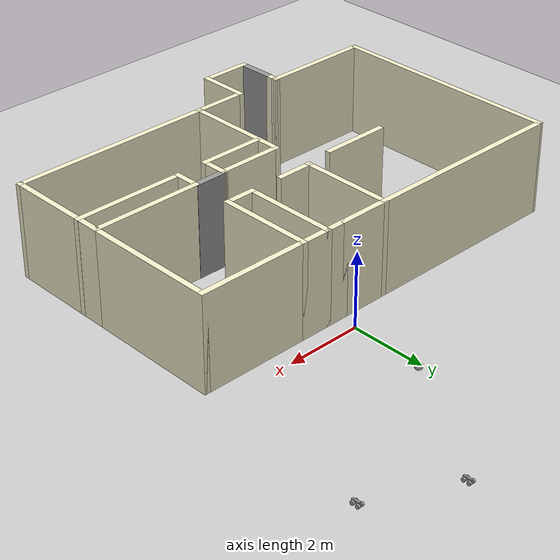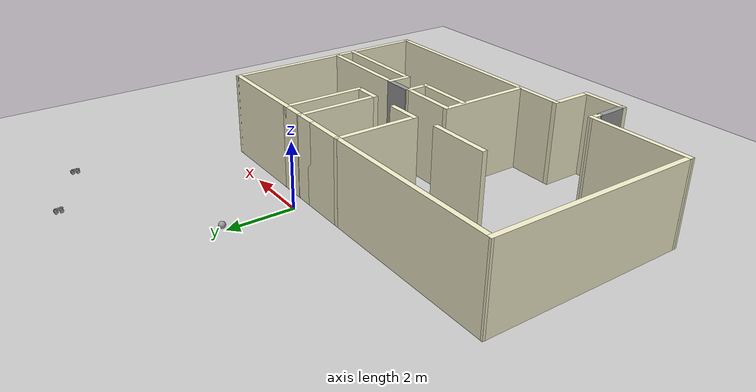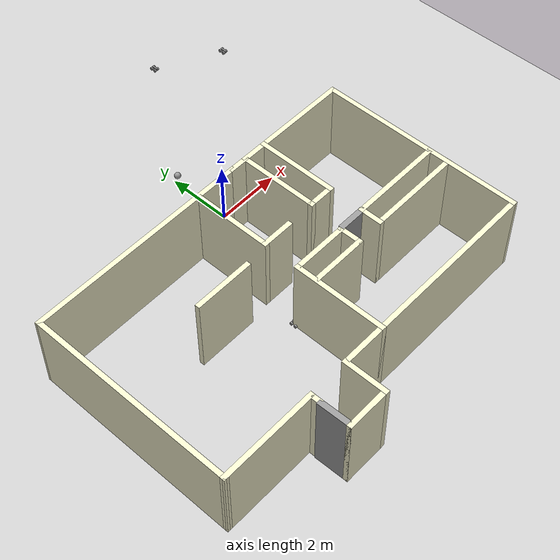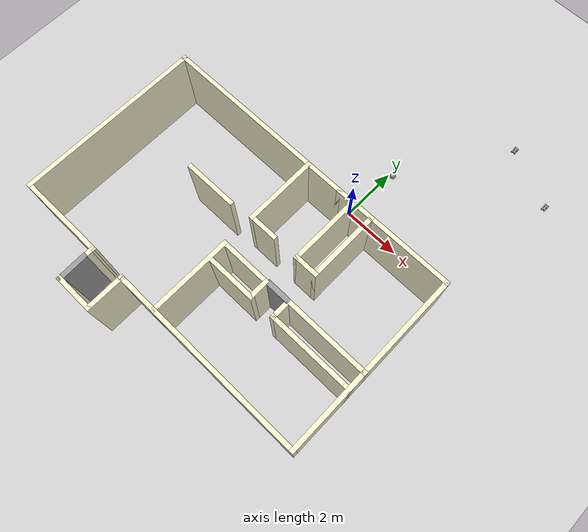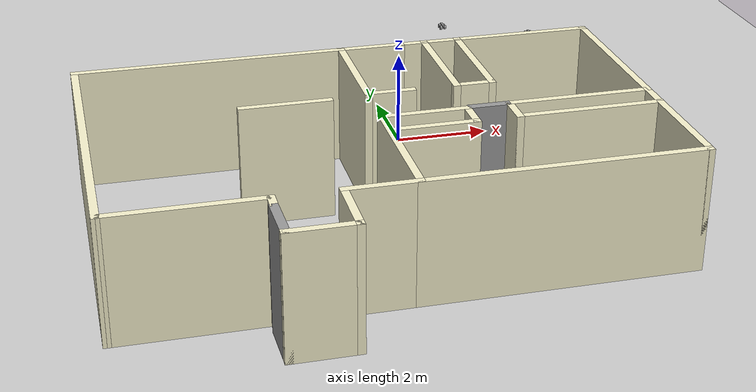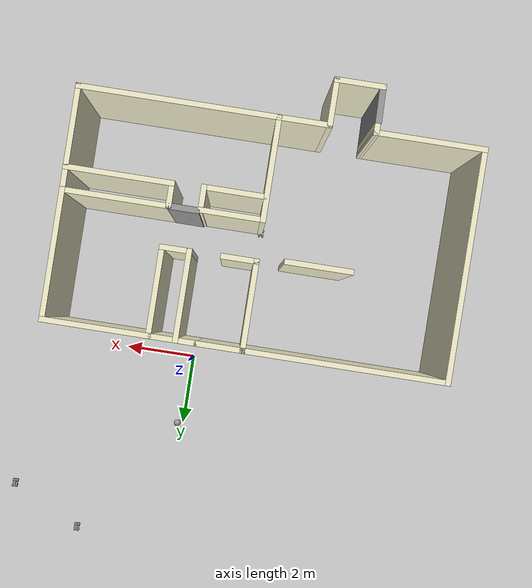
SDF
<sdf version="1.6">
 <world name="default">
  <light name="sun" type="directional">
   <pose>0 0 10 0 -0 0</pose>
   <diffuse>0.8 0.8 0.8 1</diffuse>
   <specular>0.2 0.2 0.2 1</specular>
   <attenuation>
    <range>1000</range>
    <constant>0.9</constant>
    <linear>0.01</linear>
    <quadratic>0.001</quadratic>
   </attenuation>
   <direction>-0.5 0.1 -0.9</direction>
  </light>
  <model name="house">
   <pose>-1.46609 -4.03759 0.000136 1e-06 -5e-05 0</pose>
   <link name="Door_0">
    <collision name="Door_0_Collision">
     <geometry><box><size>0.9 0.17 2.5</size></box></geometry>
     <pose>0 0 1.25 0 -0 0</pose>
    </collision>
    <visual name="Door_0_Visual">
     <pose>0 0 1.25 0 -0 0</pose>
     <geometry><box><size>0.9 0.17 2.5</size></box></geometry>
     <material>
      <script><uri>file://media/materials/scripts/gazebo.material</uri><name>Gazebo/Grey</name></script>
     </material>
    </visual>
    <pose>-2.53496 -3.43764 0 0 -0 1.59446</pose>
    <inertial>
     <inertia><ixx>1</ixx><ixy>0</ixy><ixz>0</ixz><iyy>1</iyy><iyz>0</iyz><izz>1</izz></inertia>
     <mass>1</mass>
    </inertial>
   </link>
   <link name="Door_1">
    <collision name="Door_1_Collision">
     <geometry><box><size>0.85 0.17 2.5</size></box></geometry>
     <pose>0 0 1.25 0 -0 0</pose>
    </collision>
    <visual name="Door_1_Visual">
     <pose>0 0 1.25 0 -0 0</pose>
     <geometry><box><size>0.85 0.17 2.5</size></box></geometry>
     <material>
      <script><uri>file://media/materials/scripts/gazebo.material</uri><name>Gazebo/Grey</name></script>
     </material>
    </visual>
    <pose>2.18886 0.032322 0 0 -0 0</pose>
    <inertial>
     <inertia><ixx>1</ixx><ixy>0</ixy><ixz>0</ixz><iyy>1</iyy><iyz>0</iyz><izz>1</izz></inertia>
     <mass>1</mass>
    </inertial>
   </link>
   <link name="oscar::link_1">
    <inertial>
     <mass>1</mass>
     <inertia><ixx>0.145833</ixx><ixy>0</ixy><ixz>0</ixz><iyy>0.145833</iyy><iyz>0</iyz><izz>0.125</izz></inertia>
    </inertial>
    <pose>-0.030984 -0.02472 0.043 0 -1.57079 0</pose>
    <visual name="visual">
     <geometry><cylinder><radius>0.05</radius><length>0.05</length></cylinder></geometry>
     <material>
      <lighting>1</lighting>
      <script><uri>file://media/materials/scripts/gazebo.material</uri><name>Gazebo/Grey</name></script>
      <shader type="pixel"><normal_map>__default__</normal_map></shader>
      <ambient>0.3 0.3 0.3 1</ambient>
      <diffuse>0.7 0.7 0.7 1</diffuse>
      <specular>0.01 0.01 0.01 1</specular>
      <emissive>0 0 0 1</emissive>
     </material>
    </visual>
    <collision name="collision">
     <geometry><cylinder><radius>0.05</radius><length>0.05</length></cylinder></geometry>
     <surface>
      <friction>
       <ode><mu>1</mu><mu2>1</mu2><fdir1>0 0 0</fdir1><slip1>0</slip1><slip2>0</slip2></ode>
       <torsional>
        <coefficient>1</coefficient>
        <patch_radius>0</patch_radius>
        <surface_radius>0</surface_radius>
        <use_patch_radius>1</use_patch_radius>
        <ode><slip>0</slip></ode>
       </torsional>
      </friction>
      <bounce><restitution_coefficient>0</restitution_coefficient><threshold>1e+06</threshold></bounce>
      <contact>
       <collide_without_contact>0</collide_without_contact>
       <collide_without_contact_bitmask>1</collide_without_contact_bitmask>
       <collide_bitmask>1</collide_bitmask>
       <ode>
        <soft_cfm>0</soft_cfm>
        <soft_erp>0.2</soft_erp>
        <kp>1e+13</kp>
        <kd>1</kd>
        <max_vel>0.01</max_vel>
        <min_depth>0</min_depth>
       </ode>
       <bullet>
        <split_impulse>1</split_impulse>
        <split_impulse_penetration_threshold>-0.01</split_impulse_penetration_threshold>
        <soft_cfm>0</soft_cfm>
        <soft_erp>0.2</soft_erp>
        <kp>1e+13</kp>
        <kd>1</kd>
       </bullet>
      </contact>
     </surface>
    </collision>
   </link>
   <link name="oscar::link_1_clone">
    <inertial>
     <mass>1</mass>
     <inertia><ixx>0.145833</ixx><ixy>0</ixy><ixz>0</ixz><iyy>0.145833</iyy><iyz>0</iyz><izz>0.125</izz></inertia>
    </inertial>
    <pose>-0.030984 0.115279 0.043 0 -1.57079 0</pose>
    <visual name="visual">
     <geometry><cylinder><radius>0.05</radius><length>0.05</length></cylinder></geometry>
     <material>
      <lighting>1</lighting>
      <script><uri>file://media/materials/scripts/gazebo.material</uri><name>Gazebo/Grey</name></script>
      <shader type="pixel"><normal_map>__default__</normal_map></shader>
      <ambient>0.3 0.3 0.3 1</ambient>
      <diffuse>0.7 0.7 0.7 1</diffuse>
      <specular>0.01 0.01 0.01 1</specular>
      <emissive>0 0 0 1</emissive>
     </material>
    </visual>
    <collision name="collision">
     <geometry><cylinder><radius>0.05</radius><length>0.05</length></cylinder></geometry>
     <surface>
      <friction>
       <ode><mu>1</mu><mu2>1</mu2><fdir1>0 0 0</fdir1><slip1>0</slip1><slip2>0</slip2></ode>
       <torsional>
        <coefficient>1</coefficient>
        <patch_radius>0</patch_radius>
        <surface_radius>0</surface_radius>
        <use_patch_radius>1</use_patch_radius>
        <ode><slip>0</slip></ode>
       </torsional>
      </friction>
      <bounce><restitution_coefficient>0</restitution_coefficient><threshold>1e+06</threshold></bounce>
      <contact>
       <collide_without_contact>0</collide_without_contact>
       <collide_without_contact_bitmask>1</collide_without_contact_bitmask>
       <collide_bitmask>1</collide_bitmask>
       <ode>
        <soft_cfm>0</soft_cfm>
        <soft_erp>0.2</soft_erp>
        <kp>1e+13</kp>
        <kd>1</kd>
        <max_vel>0.01</max_vel>
        <min_depth>0</min_depth>
       </ode>
       <bullet>
        <split_impulse>1</split_impulse>
        <split_impulse_penetration_threshold>-0.01</split_impulse_penetration_threshold>
        <soft_cfm>0</soft_cfm>
        <soft_erp>0.2</soft_erp>
        <kp>1e+13</kp>
        <kd>1</kd>
       </bullet>
      </contact>
     </surface>
    </collision>
   </link>
   <link name="oscar::link_2">
    <inertial>
     <mass>1</mass>
     <inertia>
      <ixx>0.166667</ixx>
      <ixy>0</ixy>
      <ixz>0</ixz>
      <iyy>0.166667</iyy>
      <iyz>0</iyz>
      <izz>0.166667</izz>
     </inertia>
     <pose>0 0 0.05 0 -0 0</pose>
    </inertial>
    <pose>0.019016 0.025279 0.093 0 -0 0</pose>
    <visual name="visual">
     <geometry><box><size>0.05 0.2 0.05</size></box></geometry>
     <material>
      <lighting>1</lighting>
      <script><uri>file://media/materials/scripts/gazebo.material</uri><name>Gazebo/Grey</name></script>
      <shader type="pixel"><normal_map>__default__</normal_map></shader>
      <ambient>0.3 0.3 0.3 1</ambient>
      <diffuse>0.7 0.7 0.7 1</diffuse>
      <specular>0.01 0.01 0.01 1</specular>
      <emissive>0 0 0 1</emissive>
     </material>
    </visual>
    <collision name="collision">
     <geometry><box><size>1 1 1</size></box></geometry>
     <surface>
      <friction>
       <ode><mu>1</mu><mu2>1</mu2><fdir1>0 0 0</fdir1><slip1>0</slip1><slip2>0</slip2></ode>
       <torsional>
        <coefficient>1</coefficient>
        <patch_radius>0</patch_radius>
        <surface_radius>0</surface_radius>
        <use_patch_radius>1</use_patch_radius>
        <ode><slip>0</slip></ode>
       </torsional>
      </friction>
      <bounce><restitution_coefficient>0</restitution_coefficient><threshold>1e+06</threshold></bounce>
      <contact>
       <collide_without_contact>0</collide_without_contact>
       <collide_without_contact_bitmask>1</collide_without_contact_bitmask>
       <collide_bitmask>1</collide_bitmask>
       <ode>
        <soft_cfm>0</soft_cfm>
        <soft_erp>0.2</soft_erp>
        <kp>1e+13</kp>
        <kd>1</kd>
        <max_vel>0.01</max_vel>
        <min_depth>0</min_depth>
       </ode>
       <bullet>
        <split_impulse>1</split_impulse>
        <split_impulse_penetration_threshold>-0.01</split_impulse_penetration_threshold>
        <soft_cfm>0</soft_cfm>
        <soft_erp>0.2</soft_erp>
        <kp>1e+13</kp>
        <kd>1</kd>
       </bullet>
      </contact>
     </surface>
    </collision>
   </link>
   <link name="oscar::link_3">
    <inertial>
     <mass>1</mass>
     <inertia><ixx>0.145833</ixx><ixy>0</ixy><ixz>0</ixz><iyy>0.145833</iyy><iyz>0</iyz><izz>0.125</izz></inertia>
    </inertial>
    <pose>0.069016 -0.024721 0.053 0 1.5707 0</pose>
    <visual name="visual">
     <geometry><cylinder><radius>0.05</radius><length>0.05</length></cylinder></geometry>
     <material>
      <lighting>1</lighting>
      <script><uri>file://media/materials/scripts/gazebo.material</uri><name>Gazebo/Grey</name></script>
      <shader type="pixel"><normal_map>__default__</normal_map></shader>
      <ambient>0.3 0.3 0.3 1</ambient>
      <diffuse>0.7 0.7 0.7 1</diffuse>
      <specular>0.01 0.01 0.01 1</specular>
      <emissive>0 0 0 1</emissive>
     </material>
    </visual>
    <collision name="collision">
     <geometry><cylinder><radius>0.05</radius><length>0.05</length></cylinder></geometry>
     <surface>
      <friction>
       <ode><mu>1</mu><mu2>1</mu2><fdir1>0 0 0</fdir1><slip1>0</slip1><slip2>0</slip2></ode>
       <torsional>
        <coefficient>1</coefficient>
        <patch_radius>0</patch_radius>
        <surface_radius>0</surface_radius>
        <use_patch_radius>1</use_patch_radius>
        <ode><slip>0</slip></ode>
       </torsional>
      </friction>
      <bounce><restitution_coefficient>0</restitution_coefficient><threshold>1e+06</threshold></bounce>
      <contact>
       <collide_without_contact>0</collide_without_contact>
       <collide_without_contact_bitmask>1</collide_without_contact_bitmask>
       <collide_bitmask>1</collide_bitmask>
       <ode>
        <soft_cfm>0</soft_cfm>
        <soft_erp>0.2</soft_erp>
        <kp>1e+13</kp>
        <kd>1</kd>
        <max_vel>0.01</max_vel>
        <min_depth>0</min_depth>
       </ode>
       <bullet>
        <split_impulse>1</split_impulse>
        <split_impulse_penetration_threshold>-0.01</split_impulse_penetration_threshold>
        <soft_cfm>0</soft_cfm>
        <soft_erp>0.2</soft_erp>
        <kp>1e+13</kp>
        <kd>1</kd>
       </bullet>
      </contact>
     </surface>
    </collision>
   </link>
   <link name="oscar::link_3_clone">
    <inertial>
     <mass>1</mass>
     <inertia><ixx>0.145833</ixx><ixy>0</ixy><ixz>0</ixz><iyy>0.145833</iyy><iyz>0</iyz><izz>0.125</izz></inertia>
    </inertial>
    <pose>0.069016 0.115274 0.043 1.5708 -1.5707 1.5708</pose>
    <visual name="visual">
     <geometry><cylinder><radius>0.05</radius><length>0.05</length></cylinder></geometry>
     <material>
      <lighting>1</lighting>
      <script><uri>file://media/materials/scripts/gazebo.material</uri><name>Gazebo/Grey</name></script>
      <shader type="pixel"><normal_map>__default__</normal_map></shader>
      <ambient>0.3 0.3 0.3 1</ambient>
      <diffuse>0.7 0.7 0.7 1</diffuse>
      <specular>0.01 0.01 0.01 1</specular>
      <emissive>0 0 0 1</emissive>
     </material>
    </visual>
    <collision name="collision">
     <geometry><cylinder><radius>0.05</radius><length>0.05</length></cylinder></geometry>
     <surface>
      <friction>
       <ode><mu>1</mu><mu2>1</mu2><fdir1>0 0 0</fdir1><slip1>0</slip1><slip2>0</slip2></ode>
       <torsional>
        <coefficient>1</coefficient>
        <patch_radius>0</patch_radius>
        <surface_radius>0</surface_radius>
        <use_patch_radius>1</use_patch_radius>
        <ode><slip>0</slip></ode>
       </torsional>
      </friction>
      <bounce><restitution_coefficient>0</restitution_coefficient><threshold>1e+06</threshold></bounce>
      <contact>
       <collide_without_contact>0</collide_without_contact>
       <collide_without_contact_bitmask>1</collide_without_contact_bitmask>
       <collide_bitmask>1</collide_bitmask>
       <ode>
        <soft_cfm>0</soft_cfm>
        <soft_erp>0.2</soft_erp>
        <kp>1e+13</kp>
        <kd>1</kd>
        <max_vel>0.01</max_vel>
        <min_depth>0</min_depth>
       </ode>
       <bullet>
        <split_impulse>1</split_impulse>
        <split_impulse_penetration_threshold>-0.01</split_impulse_penetration_threshold>
        <soft_cfm>0</soft_cfm>
        <soft_erp>0.2</soft_erp>
        <kp>1e+13</kp>
        <kd>1</kd>
       </bullet>
      </contact>
     </surface>
    </collision>
   </link>
   <joint name="oscar::link_2_JOINT_18" type="revolute">
    <parent>oscar::link_2</parent>
    <child>oscar::link_3</child>
    <axis>
     <xyz>0 0 1</xyz>
     <use_parent_model_frame>0</use_parent_model_frame>
     <limit>
      <lower>-1.79769e+308</lower>
      <upper>1.79769e+308</upper>
      <effort>-1</effort>
      <velocity>-1</velocity>
     </limit>
     <dynamics>
      <spring_reference>0</spring_reference>
      <spring_stiffness>0</spring_stiffness>
      <damping>0</damping>
     </dynamics>
    </axis>
    <physics>
     <ode><limit><cfm>0</cfm><erp>0.2</erp></limit><suspension><cfm>0</cfm><erp>0.2</erp></suspension></ode>
    </physics>
   </joint>
   <joint name="oscar::link_2_JOINT_20" type="revolute">
    <parent>oscar::link_2</parent>
    <child>oscar::link_3_clone</child>
    <axis>
     <xyz>0 0 1</xyz>
     <use_parent_model_frame>0</use_parent_model_frame>
     <limit>
      <lower>-1.79769e+308</lower>
      <upper>1.79769e+308</upper>
      <effort>-1</effort>
      <velocity>-1</velocity>
     </limit>
     <dynamics>
      <spring_reference>0</spring_reference>
      <spring_stiffness>0</spring_stiffness>
      <damping>0</damping>
     </dynamics>
    </axis>
    <physics>
     <ode><limit><cfm>0</cfm><erp>0.2</erp></limit><suspension><cfm>0</cfm><erp>0.2</erp></suspension></ode>
    </physics>
   </joint>
   <joint name="oscar::link_2_JOINT_5" type="revolute">
    <parent>oscar::link_2</parent>
    <child>oscar::link_1</child>
    <axis>
     <xyz>0 0 1</xyz>
     <use_parent_model_frame>0</use_parent_model_frame>
     <limit>
      <lower>-1.79769e+308</lower>
      <upper>1.79769e+308</upper>
      <effort>-1</effort>
      <velocity>-1</velocity>
     </limit>
     <dynamics>
      <spring_reference>0</spring_reference>
      <spring_stiffness>0</spring_stiffness>
      <damping>0</damping>
      <friction>0</friction>
     </dynamics>
    </axis>
    <physics>
     <ode><limit><cfm>0</cfm><erp>0.2</erp></limit><suspension><cfm>0</cfm><erp>0.2</erp></suspension></ode>
    </physics>
   </joint>
   <joint name="oscar::link_2_JOINT_6" type="revolute">
    <parent>oscar::link_2</parent>
    <child>oscar::link_1_clone</child>
    <axis>
     <xyz>0 0 1</xyz>
     <use_parent_model_frame>0</use_parent_model_frame>
     <limit>
      <lower>-1.79769e+308</lower>
      <upper>1.79769e+308</upper>
      <effort>-1</effort>
      <velocity>-1</velocity>
     </limit>
     <dynamics>
      <spring_reference>0</spring_reference>
      <spring_stiffness>0</spring_stiffness>
      <damping>0</damping>
      <friction>0</friction>
     </dynamics>
    </axis>
    <physics>
     <ode><limit><cfm>0</cfm><erp>0.2</erp></limit><suspension><cfm>0</cfm><erp>0.2</erp></suspension></ode>
    </physics>
   </joint>
   <static>0</static>
   <link name="Wall_10">
    <collision name="Wall_10_Collision">
     <geometry><box><size>3.063 0.15 2.5</size></box></geometry>
     <pose>0 0 1.25 0 -0 0</pose>
    </collision>
    <visual name="Wall_10_Visual">
     <pose>0 0 1.25 0 -0 0</pose>
     <geometry><box><size>3.063 0.15 2.5</size></box></geometry>
     <material>
      <script><uri>file://media/materials/scripts/gazebo.material</uri><name>Gazebo/Grey</name></script>
      <ambient>0.956863 0.941176 0.8 1</ambient>
     </material>
     <meta><layer>0</layer></meta>
    </visual>
    <pose>-3.99041 -2.74041 0 0 -0 3.14159</pose>
    <inertial>
     <inertia><ixx>1</ixx><ixy>0</ixy><ixz>0</ixz><iyy>1</iyy><iyz>0</iyz><izz>1</izz></inertia>
     <mass>1</mass>
    </inertial>
   </link>
   <link name="Wall_12">
    <collision name="Wall_12_Collision">
     <geometry><box><size>6.4 0.15 2.5</size></box></geometry>
     <pose>0 0 1.25 0 -0 0</pose>
    </collision>
    <visual name="Wall_12_Visual">
     <pose>0 0 1.25 0 -0 0</pose>
     <geometry><box><size>6.4 0.15 2.5</size></box></geometry>
     <material>
      <script><uri>file://media/materials/scripts/gazebo.material</uri><name>Gazebo/Grey</name></script>
      <ambient>0.956863 0.941176 0.8 1</ambient>
     </material>
     <meta><layer>0</layer></meta>
    </visual>
    <pose>-5.43941 0.384587 0 0 -0 1.5684</pose>
    <inertial>
     <inertia><ixx>1</ixx><ixy>0</ixy><ixz>0</ixz><iyy>1</iyy><iyz>0</iyz><izz>1</izz></inertia>
     <mass>1</mass>
    </inertial>
   </link>
   <link name="Wall_14">
    <collision name="Wall_14_Collision">
     <geometry><box><size>5.649 0.15 2.5</size></box></geometry>
     <pose>0 0 1.25 0 -0 0</pose>
    </collision>
    <visual name="Wall_14_Visual">
     <pose>0 0 1.25 0 -0 0</pose>
     <geometry><box><size>5.649 0.15 2.5</size></box></geometry>
     <material>
      <script><uri>file://media/materials/scripts/gazebo.material</uri><name>Gazebo/Grey</name></script>
      <ambient>0.956863 0.941176 0.8 1</ambient>
     </material>
     <meta><layer>0</layer></meta>
    </visual>
    <pose>-2.68241 3.50959 0 0 -0 0</pose>
    <inertial>
     <inertia><ixx>1</ixx><ixy>0</ixy><ixz>0</ixz><iyy>1</iyy><iyz>0</iyz><izz>1</izz></inertia>
     <mass>1</mass>
    </inertial>
   </link>
   <link name="Wall_18">
    <collision name="Wall_18_Collision">
     <geometry><box><size>2.53945 0.15 2.5</size></box></geometry>
     <pose>0 0 1.25 0 -0 0</pose>
    </collision>
    <visual name="Wall_18_Visual">
     <pose>0 0 1.25 0 -0 0</pose>
     <geometry><box><size>2.53945 0.15 2.5</size></box></geometry>
     <material>
      <script><uri>file://media/materials/scripts/gazebo.material</uri><name>Gazebo/Grey</name></script>
      <ambient>0.956863 0.941176 0.8 1</ambient>
     </material>
     <meta><layer>0</layer></meta>
    </visual>
    <pose>0.06709 2.31509 0 0 -0 -1.5708</pose>
    <inertial>
     <inertia><ixx>1</ixx><ixy>0</ixy><ixz>0</ixz><iyy>1</iyy><iyz>0</iyz><izz>1</izz></inertia>
     <mass>1</mass>
    </inertial>
   </link>
   <link name="Wall_2">
    <collision name="Wall_2_Collision">
     <geometry><box><size>1.397 0.15 2.5</size></box></geometry>
     <pose>0 0 1.25 0 -0 0</pose>
    </collision>
    <visual name="Wall_2_Visual">
     <pose>0 0 1.25 0 -0 0</pose>
     <geometry><box><size>1.397 0.15 2.5</size></box></geometry>
     <material>
      <script><uri>file://media/materials/scripts/gazebo.material</uri><name>Gazebo/Grey</name></script>
      <ambient>0.956863 0.941176 0.8 1</ambient>
     </material>
     <meta><layer>0</layer></meta>
    </visual>
    <pose>-1.91041 -3.96241 0 0 -0 0</pose>
    <inertial>
     <inertia><ixx>1</ixx><ixy>0</ixy><ixz>0</ixz><iyy>1</iyy><iyz>0</iyz><izz>1</izz></inertia>
     <mass>1</mass>
    </inertial>
   </link>
   <link name="Wall_22">
    <collision name="Wall_22_Collision">
     <geometry><box><size>2.896 0.15 2.5</size></box></geometry>
     <pose>0 0 1.25 0 -0 0</pose>
    </collision>
    <visual name="Wall_22_Visual">
     <pose>0 0 1.25 0 -0 0</pose>
     <geometry><box><size>2.896 0.15 2.5</size></box></geometry>
     <material>
      <script><uri>file://media/materials/scripts/gazebo.material</uri><name>Gazebo/Grey</name></script>
      <ambient>0.956863 0.941176 0.8 1</ambient>
     </material>
     <meta><layer>0</layer></meta>
    </visual>
    <pose>0.06709 -1.36741 0 0 -0 1.5708</pose>
    <inertial>
     <inertia><ixx>1</ixx><ixy>0</ixy><ixz>0</ixz><iyy>1</iyy><iyz>0</iyz><izz>1</izz></inertia>
     <mass>1</mass>
    </inertial>
   </link>
   <link name="Wall_24">
    <collision name="Wall_24_Collision">
     <geometry><box><size>1.86 0.15 2.5</size></box></geometry>
     <pose>0 0 1.25 0 -0 0</pose>
    </collision>
    <visual name="Wall_24_Visual">
     <pose>0 0 1.25 0 -0 0</pose>
     <geometry><box><size>1.86 0.15 2.5</size></box></geometry>
     <material>
      <script><uri>file://media/materials/scripts/gazebo.material</uri><name>Gazebo/Grey</name></script>
      <ambient>0.956863 0.941176 0.8 1</ambient>
     </material>
     <meta><layer>0</layer></meta>
    </visual>
    <pose>-1.58791 1.00459 0 0 -0 3.14159</pose>
    <inertial>
     <inertia><ixx>1</ixx><ixy>0</ixy><ixz>0</ixz><iyy>1</iyy><iyz>0</iyz><izz>1</izz></inertia>
     <mass>1</mass>
    </inertial>
   </link>
   <link name="Wall_26">
    <collision name="Wall_26_Collision">
     <geometry><box><size>1.43 0.15 2.5</size></box></geometry>
     <pose>0 0 1.25 0 -0 0</pose>
    </collision>
    <visual name="Wall_26_Visual">
     <pose>0 0 1.25 0 -0 0</pose>
     <geometry><box><size>1.43 0.15 2.5</size></box></geometry>
     <material>
      <script><uri>file://media/materials/scripts/gazebo.material</uri><name>Gazebo/Grey</name></script>
      <ambient>0.956863 0.941176 0.8 1</ambient>
     </material>
     <meta><layer>0</layer></meta>
    </visual>
    <pose>0.70709 3.50959 0 0 -0 0</pose>
    <inertial>
     <inertia><ixx>1</ixx><ixy>0</ixy><ixz>0</ixz><iyy>1</iyy><iyz>0</iyz><izz>1</izz></inertia>
     <mass>1</mass>
    </inertial>
   </link>
   <link name="Wall_29">
    <collision name="Wall_29_Collision">
     <geometry><box><size>1.828 0.15 2.5</size></box></geometry>
     <pose>0 0 1.25 0 -0 0</pose>
    </collision>
    <visual name="Wall_29_Visual">
     <pose>0 0 1.25 0 -0 0</pose>
     <geometry><box><size>1.828 0.15 2.5</size></box></geometry>
     <material>
      <script><uri>file://media/materials/scripts/gazebo.material</uri><name>Gazebo/Grey</name></script>
      <ambient>0.956863 0.941176 0.8 1</ambient>
     </material>
     <meta><layer>0</layer></meta>
    </visual>
    <pose>0.90609 0.005587 0 0 -0 0</pose>
    <inertial>
     <inertia><ixx>1</ixx><ixy>0</ixy><ixz>0</ixz><iyy>1</iyy><iyz>0</iyz><izz>1</izz></inertia>
     <mass>1</mass>
    </inertial>
   </link>
   <link name="Wall_39">
    <collision name="Wall_39_Collision">
     <geometry><box><size>2.997 0.15 2.5</size></box></geometry>
     <pose>0 0 1.25 0 -0 0</pose>
    </collision>
    <visual name="Wall_39_Visual">
     <pose>0 0 1.25 0 -0 0</pose>
     <geometry><box><size>2.997 0.15 2.5</size></box></geometry>
     <material>
      <script><uri>file://media/materials/scripts/gazebo.material</uri><name>Gazebo/Grey</name></script>
      <ambient>0.956863 0.941176 0.8 1</ambient>
     </material>
     <meta><layer>0</layer></meta>
    </visual>
    <pose>4.02059 0.034587 0 0 -0 3.14159</pose>
    <inertial>
     <inertia><ixx>1</ixx><ixy>0</ixy><ixz>0</ixz><iyy>1</iyy><iyz>0</iyz><izz>1</izz></inertia>
     <mass>1</mass>
    </inertial>
   </link>
   <link name="Wall_4">
    <collision name="Wall_4_Collision">
     <geometry><box><size>1.37235 0.15 2.5</size></box></geometry>
     <pose>0 0 1.25 0 -0 0</pose>
    </collision>
    <visual name="Wall_4_Visual">
     <pose>0 0 1.25 0 -0 0</pose>
     <geometry><box><size>1.37235 0.15 2.5</size></box></geometry>
     <material>
      <script><uri>file://media/materials/scripts/gazebo.material</uri><name>Gazebo/Grey</name></script>
      <ambient>0.956863 0.941176 0.8 1</ambient>
     </material>
     <meta><layer>0</layer></meta>
    </visual>
    <pose>-1.28691 -3.35141 0 0 -0 1.5708</pose>
    <inertial>
     <inertia><ixx>1</ixx><ixy>0</ixy><ixz>0</ixz><iyy>1</iyy><iyz>0</iyz><izz>1</izz></inertia>
     <mass>1</mass>
    </inertial>
   </link>
   <link name="Wall_6">
    <collision name="Wall_6_Collision">
     <geometry><box><size>1.504 0.15 2.5</size></box></geometry>
     <pose>0 0 1.25 0 -0 0</pose>
    </collision>
    <visual name="Wall_6_Visual">
     <pose>0 0 1.25 0 -0 0</pose>
     <geometry><box><size>1.504 0.15 2.5</size></box></geometry>
     <material>
      <script><uri>file://media/materials/scripts/gazebo.material</uri><name>Gazebo/Grey</name></script>
      <ambient>0.956863 0.941176 0.8 1</ambient>
     </material>
     <meta><layer>0</layer></meta>
    </visual>
    <pose>-0.60991 -2.74041 0 0 -0 0</pose>
    <inertial>
     <inertia><ixx>1</ixx><ixy>0</ixy><ixz>0</ixz><iyy>1</iyy><iyz>0</iyz><izz>1</izz></inertia>
     <mass>1</mass>
    </inertial>
   </link>
   <link name="Wall_64">
    <collision name="Wall_64_Collision">
     <geometry><box><size>1.041 0.15 2.5</size></box></geometry>
     <pose>0 0 1.25 0 -0 0</pose>
    </collision>
    <visual name="Wall_64_Visual">
     <pose>0 0 1.25 0 -0 0</pose>
     <geometry><box><size>1.041 0.15 2.5</size></box></geometry>
     <material>
      <script><uri>file://media/materials/scripts/gazebo.material</uri><name>Gazebo/Grey</name></script>
      <ambient>0.956863 0.941176 0.8 1</ambient>
     </material>
     <meta><layer>0</layer></meta>
    </visual>
    <pose>0.51259 1.12059 0 0 -0 0</pose>
    <inertial>
     <inertia><ixx>1</ixx><ixy>0</ixy><ixz>0</ixz><iyy>1</iyy><iyz>0</iyz><izz>1</izz></inertia>
     <mass>1</mass>
    </inertial>
   </link>
   <link name="Wall_66">
    <collision name="Wall_66_Collision">
     <geometry><box><size>0.88 0.15 2.5</size></box></geometry>
     <pose>0 0 1.25 0 -0 0</pose>
    </collision>
    <visual name="Wall_66_Visual">
     <pose>0 0 1.25 0 -0 0</pose>
     <geometry><box><size>0.88 0.15 2.5</size></box></geometry>
     <material>
      <script><uri>file://media/materials/scripts/gazebo.material</uri><name>Gazebo/Grey</name></script>
      <ambient>0.956863 0.941176 0.8 1</ambient>
     </material>
     <meta><layer>0</layer></meta>
    </visual>
    <pose>2.23209 1.12859 0 0 -0 0</pose>
    <inertial>
     <inertia><ixx>1</ixx><ixy>0</ixy><ixz>0</ixz><iyy>1</iyy><iyz>0</iyz><izz>1</izz></inertia>
     <mass>1</mass>
    </inertial>
   </link>
   <link name="Wall_68">
    <collision name="Wall_68_Collision">
     <geometry><box><size>2.531 0.15 2.5</size></box></geometry>
     <pose>0 0 1.25 0 -0 0</pose>
    </collision>
    <visual name="Wall_68_Visual">
     <pose>0 0 1.25 0 -0 0</pose>
     <geometry><box><size>2.531 0.15 2.5</size></box></geometry>
     <material>
      <script><uri>file://media/materials/scripts/gazebo.material</uri><name>Gazebo/Grey</name></script>
      <ambient>0.956863 0.941176 0.8 1</ambient>
     </material>
     <meta><layer>0</layer></meta>
    </visual>
    <pose>1.86709 2.31909 0 0 -0 1.5708</pose>
    <inertial>
     <inertia><ixx>1</ixx><ixy>0</ixy><ixz>0</ixz><iyy>1</iyy><iyz>0</iyz><izz>1</izz></inertia>
     <mass>1</mass>
    </inertial>
   </link>
   <link name="Wall_70">
    <collision name="Wall_70_Collision">
     <geometry><box><size>0.67 0.15 2.5</size></box></geometry>
     <pose>0 0 1.25 0 -0 0</pose>
    </collision>
    <visual name="Wall_70_Visual">
     <pose>0 0 1.25 0 -0 0</pose>
     <geometry><box><size>0.67 0.15 2.5</size></box></geometry>
     <material>
      <script><uri>file://media/materials/scripts/gazebo.material</uri><name>Gazebo/Grey</name></script>
      <ambient>0.956863 0.941176 0.8 1</ambient>
     </material>
     <meta><layer>0</layer></meta>
    </visual>
    <pose>1.60709 3.50959 0 0 -0 0</pose>
    <inertial>
     <inertia><ixx>1</ixx><ixy>0</ixy><ixz>0</ixz><iyy>1</iyy><iyz>0</iyz><izz>1</izz></inertia>
     <mass>1</mass>
    </inertial>
   </link>
   <link name="Wall_72">
    <collision name="Wall_72_Collision">
     <geometry><box><size>2.531 0.15 2.5</size></box></geometry>
     <pose>0 0 1.25 0 -0 0</pose>
    </collision>
    <visual name="Wall_72_Visual">
     <pose>0 0 1.25 0 -0 0</pose>
     <geometry><box><size>2.531 0.15 2.5</size></box></geometry>
     <material>
      <script><uri>file://media/materials/scripts/gazebo.material</uri><name>Gazebo/Grey</name></script>
      <ambient>0.956863 0.941176 0.8 1</ambient>
     </material>
     <meta><layer>0</layer></meta>
    </visual>
    <pose>2.59709 2.31909 0 0 -0 1.5708</pose>
    <inertial>
     <inertia><ixx>1</ixx><ixy>0</ixy><ixz>0</ixz><iyy>1</iyy><iyz>0</iyz><izz>1</izz></inertia>
     <mass>1</mass>
    </inertial>
   </link>
   <link name="Wall_75">
    <collision name="Wall_75_Collision">
     <geometry><box><size>2.997 0.15 2.5</size></box></geometry>
     <pose>0 0 1.25 0 -0 0</pose>
    </collision>
    <visual name="Wall_75_Visual">
     <pose>0 0 1.25 0 -0 0</pose>
     <geometry><box><size>2.997 0.15 2.5</size></box></geometry>
     <material>
      <script><uri>file://media/materials/scripts/gazebo.material</uri><name>Gazebo/Grey</name></script>
      <ambient>0.956863 0.941176 0.8 1</ambient>
     </material>
     <meta><layer>0</layer></meta>
    </visual>
    <pose>4.02059 3.50959 0 0 -0 0</pose>
    <inertial>
     <inertia><ixx>1</ixx><ixy>0</ixy><ixz>0</ixz><iyy>1</iyy><iyz>0</iyz><izz>1</izz></inertia>
     <mass>1</mass>
    </inertial>
   </link>
   <link name="Wall_77">
    <collision name="Wall_77_Collision">
     <geometry><box><size>3.625 0.15 2.5</size></box></geometry>
     <pose>0 0 1.25 0 -0 0</pose>
    </collision>
    <visual name="Wall_77_Visual">
     <pose>0 0 1.25 0 -0 0</pose>
     <geometry><box><size>3.625 0.15 2.5</size></box></geometry>
     <material>
      <script><uri>file://media/materials/scripts/gazebo.material</uri><name>Gazebo/Grey</name></script>
      <ambient>0.956863 0.941176 0.8 1</ambient>
     </material>
     <meta><layer>0</layer></meta>
    </visual>
    <pose>5.44409 1.77209 0 0 -0 -1.5708</pose>
    <inertial>
     <inertia><ixx>1</ixx><ixy>0</ixy><ixz>0</ixz><iyy>1</iyy><iyz>0</iyz><izz>1</izz></inertia>
     <mass>1</mass>
    </inertial>
   </link>
   <link name="Wall_79">
    <collision name="Wall_79_Collision">
     <geometry><box><size>2.925 0.15 2.5</size></box></geometry>
     <pose>0 0 1.25 0 -0 0</pose>
    </collision>
    <visual name="Wall_79_Visual">
     <pose>0 0 1.25 0 -0 0</pose>
     <geometry><box><size>2.925 0.15 2.5</size></box></geometry>
     <material>
      <script><uri>file://media/materials/scripts/gazebo.material</uri><name>Gazebo/Grey</name></script>
      <ambient>0.956863 0.941176 0.8 1</ambient>
     </material>
     <meta><layer>0</layer></meta>
    </visual>
    <pose>5.44409 -1.35291 0 0 -0 -1.5708</pose>
    <inertial>
     <inertia><ixx>1</ixx><ixy>0</ixy><ixz>0</ixz><iyy>1</iyy><iyz>0</iyz><izz>1</izz></inertia>
     <mass>1</mass>
    </inertial>
   </link>
   <link name="Wall_81">
    <collision name="Wall_81_Collision">
     <geometry><box><size>5.527 0.15 2.5</size></box></geometry>
     <pose>0 0 1.25 0 -0 0</pose>
    </collision>
    <visual name="Wall_81_Visual">
     <pose>0 0 1.25 0 -0 0</pose>
     <geometry><box><size>5.527 0.15 2.5</size></box></geometry>
     <material>
      <script><uri>file://media/materials/scripts/gazebo.material</uri><name>Gazebo/Grey</name></script>
      <ambient>0.956863 0.941176 0.8 1</ambient>
     </material>
     <meta><layer>0</layer></meta>
    </visual>
    <pose>2.75559 -2.74041 0 0 -0 0</pose>
    <inertial>
     <inertia><ixx>1</ixx><ixy>0</ixy><ixz>0</ixz><iyy>1</iyy><iyz>0</iyz><izz>1</izz></inertia>
     <mass>1</mass>
    </inertial>
   </link>
   <link name="Wall_83">
    <collision name="Wall_83_Collision">
     <geometry><box><size>0.88 0.15 2.5</size></box></geometry>
     <pose>0 0 1.25 0 -0 0</pose>
    </collision>
    <visual name="Wall_83_Visual">
     <pose>0 0 1.25 0 -0 0</pose>
     <geometry><box><size>0.88 0.15 2.5</size></box></geometry>
     <material>
      <script><uri>file://media/materials/scripts/gazebo.material</uri><name>Gazebo/Grey</name></script>
      <ambient>0.956863 0.941176 0.8 1</ambient>
     </material>
     <meta><layer>0</layer></meta>
    </visual>
    <pose>2.23209 3.50959 0 0 -0 0</pose>
    <inertial>
     <inertia><ixx>1</ixx><ixy>0</ixy><ixz>0</ixz><iyy>1</iyy><iyz>0</iyz><izz>1</izz></inertia>
     <mass>1</mass>
    </inertial>
   </link>
   <link name="Wall_85">
    <collision name="Wall_85_Collision">
     <geometry><box><size>0.762 0.15 2.5</size></box></geometry>
     <pose>0 0 1.25 0 -0 0</pose>
    </collision>
    <visual name="Wall_85_Visual">
     <pose>0 0 1.25 0 -0 0</pose>
     <geometry><box><size>0.762 0.15 2.5</size></box></geometry>
     <material>
      <script><uri>file://media/materials/scripts/gazebo.material</uri><name>Gazebo/Grey</name></script>
      <ambient>0.956863 0.941176 0.8 1</ambient>
     </material>
     <meta><layer>0</layer></meta>
    </visual>
    <pose>1.74509 -0.300413 0 0 -0 -1.5708</pose>
    <inertial>
     <inertia><ixx>1</ixx><ixy>0</ixy><ixz>0</ixz><iyy>1</iyy><iyz>0</iyz><izz>1</izz></inertia>
     <mass>1</mass>
    </inertial>
   </link>
   <link name="Wall_87">
    <collision name="Wall_87_Collision">
     <geometry><box><size>1.75 0.15 2.5</size></box></geometry>
     <pose>0 0 1.25 0 -0 0</pose>
    </collision>
    <visual name="Wall_87_Visual">
     <pose>0 0 1.25 0 -0 0</pose>
     <geometry><box><size>1.75 0.15 2.5</size></box></geometry>
     <material>
      <script><uri>file://media/materials/scripts/gazebo.material</uri><name>Gazebo/Grey</name></script>
      <ambient>0.956863 0.941176 0.8 1</ambient>
     </material>
     <meta><layer>0</layer></meta>
    </visual>
    <pose>0.94509 -0.606413 0 0 -0 3.14159</pose>
    <inertial>
     <inertia><ixx>1</ixx><ixy>0</ixy><ixz>0</ixz><iyy>1</iyy><iyz>0</iyz><izz>1</izz></inertia>
     <mass>1</mass>
    </inertial>
   </link>
   <link name="Wall_89">
    <collision name="Wall_89_Collision">
     <geometry><box><size>0.762 0.15 2.5</size></box></geometry>
     <pose>0 0 1.25 0 -0 0</pose>
    </collision>
    <visual name="Wall_89_Visual">
     <pose>0 0 1.25 0 -0 0</pose>
     <geometry><box><size>0.762 0.15 2.5</size></box></geometry>
     <material>
      <script><uri>file://media/materials/scripts/gazebo.material</uri><name>Gazebo/Grey</name></script>
      <ambient>0.956863 0.941176 0.8 1</ambient>
     </material>
     <meta><layer>0</layer></meta>
    </visual>
    <pose>2.59709 -0.271413 0 0 -0 -1.5708</pose>
    <inertial>
     <inertia><ixx>1</ixx><ixy>0</ixy><ixz>0</ixz><iyy>1</iyy><iyz>0</iyz><izz>1</izz></inertia>
     <mass>1</mass>
    </inertial>
   </link>
   <link name="Wall_91">
    <collision name="Wall_91_Collision">
     <geometry><box><size>3 0.15 2.5</size></box></geometry>
     <pose>0 0 1.25 0 -0 0</pose>
    </collision>
    <visual name="Wall_91_Visual">
     <pose>0 0 1.25 0 -0 0</pose>
     <geometry><box><size>3 0.15 2.5</size></box></geometry>
     <material>
      <script><uri>file://media/materials/scripts/gazebo.material</uri><name>Gazebo/Grey</name></script>
      <ambient>0.956863 0.941176 0.8 1</ambient>
     </material>
     <meta><layer>0</layer></meta>
    </visual>
    <pose>4.02209 -0.577413 0 0 -0 0</pose>
    <inertial>
     <inertia><ixx>1</ixx><ixy>0</ixy><ixz>0</ixz><iyy>1</iyy><iyz>0</iyz><izz>1</izz></inertia>
     <mass>1</mass>
    </inertial>
   </link>
   <link name="Wall_93">
    <collision name="Wall_93_Collision">
     <geometry><box><size>0.16 0.15 2.5</size></box></geometry>
     <pose>0 0 1.25 0 -0 0</pose>
    </collision>
    <visual name="Wall_93_Visual">
     <pose>0 0 1.25 0 -0 0</pose>
     <geometry><box><size>0.16 0.15 2.5</size></box></geometry>
     <material>
      <script><uri>file://media/materials/scripts/gazebo.material</uri><name>Gazebo/Grey</name></script>
      <ambient>0.956863 0.941176 0.8 1</ambient>
     </material>
     <meta><layer>0</layer></meta>
    </visual>
    <pose>-2.53391 -3.95741 0 0 -0 1.5708</pose>
    <inertial>
     <inertia><ixx>1</ixx><ixy>0</ixy><ixz>0</ixz><iyy>1</iyy><iyz>0</iyz><izz>1</izz></inertia>
     <mass>1</mass>
    </inertial>
   </link>
   <link name="Wall_95">
    <collision name="Wall_95_Collision">
     <geometry><box><size>0.409839 0.15 2.5</size></box></geometry>
     <pose>0 0 1.25 0 -0 0</pose>
    </collision>
    <visual name="Wall_95_Visual">
     <pose>0 0 1.25 0 -0 0</pose>
     <geometry><box><size>0.409839 0.15 2.5</size></box></geometry>
     <material>
      <script><uri>file://media/materials/scripts/gazebo.material</uri><name>Gazebo/Grey</name></script>
      <ambient>0.956863 0.941176 0.8 1</ambient>
     </material>
     <meta><layer>0</layer></meta>
    </visual>
    <pose>-2.53444 -2.87033 0 0 -0 1.56675</pose>
    <inertial>
     <inertia><ixx>1</ixx><ixy>0</ixy><ixz>0</ixz><iyy>1</iyy><iyz>0</iyz><izz>1</izz></inertia>
     <mass>1</mass>
    </inertial>
   </link>
   <static>1</static>
  </model>
  <model name="ground_plane">
   <static>1</static>
   <link name="link">
    <collision name="collision">
     <geometry><plane><normal>0 0 1</normal><size>100 100</size></plane></geometry>
     <surface>
      <contact><collide_bitmask>65535</collide_bitmask></contact>
      <friction><ode><mu>100</mu><mu2>50</mu2></ode></friction>
     </surface>
    </collision>
    <visual name="visual">
     <cast_shadows>0</cast_shadows>
     <geometry><plane><normal>0 0 1</normal><size>100 100</size></plane></geometry>
     <material>
      <script><uri>file://media/materials/scripts/gazebo.material</uri><name>Gazebo/Grey</name></script>
     </material>
    </visual>
   </link>
  </model>
  <gravity>0 0 -9.8</gravity>
  <magnetic_field>6e-06 2.3e-05 -4.2e-05</magnetic_field>
  <atmosphere type="adiabatic"/>
  <physics name="default_physics" default="0" type="ode">
   <max_step_size>0.001</max_step_size>
   <real_time_factor>1</real_time_factor>
   <real_time_update_rate>1000</real_time_update_rate>
  </physics>
  <scene><ambient>0.4 0.4 0.4 1</ambient><background>0.7 0.7 0.7 1</background><shadows>1</shadows></scene>
  <audio><device>default</device></audio>
  <spherical_coordinates>
   <surface_model>EARTH_WGS84</surface_model>
   <latitude_deg>0</latitude_deg>
   <longitude_deg>0</longitude_deg>
   <elevation>0</elevation>
   <heading_deg>0</heading_deg>
  </spherical_coordinates>
  <model name="oscar">
   <link name="link_1">
    <inertial>
     <mass>1</mass>
     <inertia><ixx>0.145833</ixx><ixy>0</ixy><ixz>0</ixz><iyy>0.145833</iyy><iyz>0</iyz><izz>0.125</izz></inertia>
    </inertial>
    <pose>-0.030984 -0.02472 0.043 0 -1.57079 0</pose>
    <visual name="visual">
     <geometry><cylinder><radius>0.05</radius><length>0.05</length></cylinder></geometry>
     <material>
      <lighting>1</lighting>
      <script><uri>file://media/materials/scripts/gazebo.material</uri><name>Gazebo/Grey</name></script>
      <shader type="pixel"><normal_map>__default__</normal_map></shader>
      <ambient>0.3 0.3 0.3 1</ambient>
      <diffuse>0.7 0.7 0.7 1</diffuse>
      <specular>0.01 0.01 0.01 1</specular>
      <emissive>0 0 0 1</emissive>
     </material>
    </visual>
    <collision name="collision">
     <geometry><cylinder><radius>0.05</radius><length>0.05</length></cylinder></geometry>
     <surface>
      <friction>
       <ode><mu>1</mu><mu2>1</mu2><fdir1>0 0 0</fdir1><slip1>0</slip1><slip2>0</slip2></ode>
       <torsional>
        <coefficient>1</coefficient>
        <patch_radius>0</patch_radius>
        <surface_radius>0</surface_radius>
        <use_patch_radius>1</use_patch_radius>
        <ode><slip>0</slip></ode>
       </torsional>
      </friction>
      <bounce><restitution_coefficient>0</restitution_coefficient><threshold>1e+06</threshold></bounce>
      <contact>
       <collide_without_contact>0</collide_without_contact>
       <collide_without_contact_bitmask>1</collide_without_contact_bitmask>
       <collide_bitmask>1</collide_bitmask>
       <ode>
        <soft_cfm>0</soft_cfm>
        <soft_erp>0.2</soft_erp>
        <kp>1e+13</kp>
        <kd>1</kd>
        <max_vel>0.01</max_vel>
        <min_depth>0</min_depth>
       </ode>
       <bullet>
        <split_impulse>1</split_impulse>
        <split_impulse_penetration_threshold>-0.01</split_impulse_penetration_threshold>
        <soft_cfm>0</soft_cfm>
        <soft_erp>0.2</soft_erp>
        <kp>1e+13</kp>
        <kd>1</kd>
       </bullet>
      </contact>
     </surface>
    </collision>
   </link>
   <link name="link_1_clone">
    <inertial>
     <mass>1</mass>
     <inertia><ixx>0.145833</ixx><ixy>0</ixy><ixz>0</ixz><iyy>0.145833</iyy><iyz>0</iyz><izz>0.125</izz></inertia>
    </inertial>
    <pose>-0.030984 0.115279 0.043 0 -1.57079 0</pose>
    <visual name="visual">
     <geometry><cylinder><radius>0.05</radius><length>0.05</length></cylinder></geometry>
     <material>
      <lighting>1</lighting>
      <script><uri>file://media/materials/scripts/gazebo.material</uri><name>Gazebo/Grey</name></script>
      <shader type="pixel"><normal_map>__default__</normal_map></shader>
      <ambient>0.3 0.3 0.3 1</ambient>
      <diffuse>0.7 0.7 0.7 1</diffuse>
      <specular>0.01 0.01 0.01 1</specular>
      <emissive>0 0 0 1</emissive>
     </material>
    </visual>
    <collision name="collision">
     <geometry><cylinder><radius>0.05</radius><length>0.05</length></cylinder></geometry>
     <surface>
      <friction>
       <ode><mu>1</mu><mu2>1</mu2><fdir1>0 0 0</fdir1><slip1>0</slip1><slip2>0</slip2></ode>
       <torsional>
        <coefficient>1</coefficient>
        <patch_radius>0</patch_radius>
        <surface_radius>0</surface_radius>
        <use_patch_radius>1</use_patch_radius>
        <ode><slip>0</slip></ode>
       </torsional>
      </friction>
      <bounce><restitution_coefficient>0</restitution_coefficient><threshold>1e+06</threshold></bounce>
      <contact>
       <collide_without_contact>0</collide_without_contact>
       <collide_without_contact_bitmask>1</collide_without_contact_bitmask>
       <collide_bitmask>1</collide_bitmask>
       <ode>
        <soft_cfm>0</soft_cfm>
        <soft_erp>0.2</soft_erp>
        <kp>1e+13</kp>
        <kd>1</kd>
        <max_vel>0.01</max_vel>
        <min_depth>0</min_depth>
       </ode>
       <bullet>
        <split_impulse>1</split_impulse>
        <split_impulse_penetration_threshold>-0.01</split_impulse_penetration_threshold>
        <soft_cfm>0</soft_cfm>
        <soft_erp>0.2</soft_erp>
        <kp>1e+13</kp>
        <kd>1</kd>
       </bullet>
      </contact>
     </surface>
    </collision>
   </link>
   <link name="link_2">
    <inertial>
     <mass>1</mass>
     <inertia>
      <ixx>0.166667</ixx>
      <ixy>0</ixy>
      <ixz>0</ixz>
      <iyy>0.166667</iyy>
      <iyz>0</iyz>
      <izz>0.166667</izz>
     </inertia>
     <pose>0 0 0.05 0 -0 0</pose>
    </inertial>
    <pose>0.019016 0.025279 0.093 0 -0 0</pose>
    <visual name="visual">
     <geometry><box><size>0.05 0.2 0.05</size></box></geometry>
     <material>
      <lighting>1</lighting>
      <script><uri>file://media/materials/scripts/gazebo.material</uri><name>Gazebo/Grey</name></script>
      <shader type="pixel"><normal_map>__default__</normal_map></shader>
      <ambient>0.3 0.3 0.3 1</ambient>
      <diffuse>0.7 0.7 0.7 1</diffuse>
      <specular>0.01 0.01 0.01 1</specular>
      <emissive>0 0 0 1</emissive>
     </material>
    </visual>
    <collision name="collision">
     <geometry><box><size>1 1 1</size></box></geometry>
     <surface>
      <friction>
       <ode><mu>1</mu><mu2>1</mu2><fdir1>0 0 0</fdir1><slip1>0</slip1><slip2>0</slip2></ode>
       <torsional>
        <coefficient>1</coefficient>
        <patch_radius>0</patch_radius>
        <surface_radius>0</surface_radius>
        <use_patch_radius>1</use_patch_radius>
        <ode><slip>0</slip></ode>
       </torsional>
      </friction>
      <bounce><restitution_coefficient>0</restitution_coefficient><threshold>1e+06</threshold></bounce>
      <contact>
       <collide_without_contact>0</collide_without_contact>
       <collide_without_contact_bitmask>1</collide_without_contact_bitmask>
       <collide_bitmask>1</collide_bitmask>
       <ode>
        <soft_cfm>0</soft_cfm>
        <soft_erp>0.2</soft_erp>
        <kp>1e+13</kp>
        <kd>1</kd>
        <max_vel>0.01</max_vel>
        <min_depth>0</min_depth>
       </ode>
       <bullet>
        <split_impulse>1</split_impulse>
        <split_impulse_penetration_threshold>-0.01</split_impulse_penetration_threshold>
        <soft_cfm>0</soft_cfm>
        <soft_erp>0.2</soft_erp>
        <kp>1e+13</kp>
        <kd>1</kd>
       </bullet>
      </contact>
     </surface>
    </collision>
   </link>
   <link name="link_3">
    <inertial>
     <mass>1</mass>
     <inertia><ixx>0.145833</ixx><ixy>0</ixy><ixz>0</ixz><iyy>0.145833</iyy><iyz>0</iyz><izz>0.125</izz></inertia>
    </inertial>
    <pose>0.069016 -0.024721 0.053 0 1.5707 0</pose>
    <visual name="visual">
     <geometry><cylinder><radius>0.05</radius><length>0.05</length></cylinder></geometry>
     <material>
      <lighting>1</lighting>
      <script><uri>file://media/materials/scripts/gazebo.material</uri><name>Gazebo/Grey</name></script>
      <shader type="pixel"><normal_map>__default__</normal_map></shader>
      <ambient>0.3 0.3 0.3 1</ambient>
      <diffuse>0.7 0.7 0.7 1</diffuse>
      <specular>0.01 0.01 0.01 1</specular>
      <emissive>0 0 0 1</emissive>
     </material>
    </visual>
    <collision name="collision">
     <geometry><cylinder><radius>0.05</radius><length>0.05</length></cylinder></geometry>
     <surface>
      <friction>
       <ode><mu>1</mu><mu2>1</mu2><fdir1>0 0 0</fdir1><slip1>0</slip1><slip2>0</slip2></ode>
       <torsional>
        <coefficient>1</coefficient>
        <patch_radius>0</patch_radius>
        <surface_radius>0</surface_radius>
        <use_patch_radius>1</use_patch_radius>
        <ode><slip>0</slip></ode>
       </torsional>
      </friction>
      <bounce><restitution_coefficient>0</restitution_coefficient><threshold>1e+06</threshold></bounce>
      <contact>
       <collide_without_contact>0</collide_without_contact>
       <collide_without_contact_bitmask>1</collide_without_contact_bitmask>
       <collide_bitmask>1</collide_bitmask>
       <ode>
        <soft_cfm>0</soft_cfm>
        <soft_erp>0.2</soft_erp>
        <kp>1e+13</kp>
        <kd>1</kd>
        <max_vel>0.01</max_vel>
        <min_depth>0</min_depth>
       </ode>
       <bullet>
        <split_impulse>1</split_impulse>
        <split_impulse_penetration_threshold>-0.01</split_impulse_penetration_threshold>
        <soft_cfm>0</soft_cfm>
        <soft_erp>0.2</soft_erp>
        <kp>1e+13</kp>
        <kd>1</kd>
       </bullet>
      </contact>
     </surface>
    </collision>
   </link>
   <link name="link_3_clone">
    <inertial>
     <mass>1</mass>
     <inertia><ixx>0.145833</ixx><ixy>0</ixy><ixz>0</ixz><iyy>0.145833</iyy><iyz>0</iyz><izz>0.125</izz></inertia>
    </inertial>
    <pose>0.069016 0.115274 0.043 1.5708 -1.5707 1.5708</pose>
    <visual name="visual">
     <geometry><cylinder><radius>0.05</radius><length>0.05</length></cylinder></geometry>
     <material>
      <lighting>1</lighting>
      <script><uri>file://media/materials/scripts/gazebo.material</uri><name>Gazebo/Grey</name></script>
      <shader type="pixel"><normal_map>__default__</normal_map></shader>
      <ambient>0.3 0.3 0.3 1</ambient>
      <diffuse>0.7 0.7 0.7 1</diffuse>
      <specular>0.01 0.01 0.01 1</specular>
      <emissive>0 0 0 1</emissive>
     </material>
    </visual>
    <collision name="collision">
     <geometry><cylinder><radius>0.05</radius><length>0.05</length></cylinder></geometry>
     <surface>
      <friction>
       <ode><mu>1</mu><mu2>1</mu2><fdir1>0 0 0</fdir1><slip1>0</slip1><slip2>0</slip2></ode>
       <torsional>
        <coefficient>1</coefficient>
        <patch_radius>0</patch_radius>
        <surface_radius>0</surface_radius>
        <use_patch_radius>1</use_patch_radius>
        <ode><slip>0</slip></ode>
       </torsional>
      </friction>
      <bounce><restitution_coefficient>0</restitution_coefficient><threshold>1e+06</threshold></bounce>
      <contact>
       <collide_without_contact>0</collide_without_contact>
       <collide_without_contact_bitmask>1</collide_without_contact_bitmask>
       <collide_bitmask>1</collide_bitmask>
       <ode>
        <soft_cfm>0</soft_cfm>
        <soft_erp>0.2</soft_erp>
        <kp>1e+13</kp>
        <kd>1</kd>
        <max_vel>0.01</max_vel>
        <min_depth>0</min_depth>
       </ode>
       <bullet>
        <split_impulse>1</split_impulse>
        <split_impulse_penetration_threshold>-0.01</split_impulse_penetration_threshold>
        <soft_cfm>0</soft_cfm>
        <soft_erp>0.2</soft_erp>
        <kp>1e+13</kp>
        <kd>1</kd>
       </bullet>
      </contact>
     </surface>
    </collision>
   </link>
   <joint name="link_2_JOINT_18" type="revolute">
    <parent>link_2</parent>
    <child>link_3</child>
    <axis>
     <xyz>0 0 1</xyz>
     <use_parent_model_frame>0</use_parent_model_frame>
     <limit>
      <lower>-1.79769e+308</lower>
      <upper>1.79769e+308</upper>
      <effort>-1</effort>
      <velocity>-1</velocity>
     </limit>
     <dynamics>
      <spring_reference>0</spring_reference>
      <spring_stiffness>0</spring_stiffness>
      <damping>0</damping>
     </dynamics>
    </axis>
    <physics>
     <ode><limit><cfm>0</cfm><erp>0.2</erp></limit><suspension><cfm>0</cfm><erp>0.2</erp></suspension></ode>
    </physics>
   </joint>
   <joint name="link_2_JOINT_20" type="revolute">
    <parent>link_2</parent>
    <child>link_3_clone</child>
    <axis>
     <xyz>0 0 1</xyz>
     <use_parent_model_frame>0</use_parent_model_frame>
     <limit>
      <lower>-1.79769e+308</lower>
      <upper>1.79769e+308</upper>
      <effort>-1</effort>
      <velocity>-1</velocity>
     </limit>
     <dynamics>
      <spring_reference>0</spring_reference>
      <spring_stiffness>0</spring_stiffness>
      <damping>0</damping>
     </dynamics>
    </axis>
    <physics>
     <ode><limit><cfm>0</cfm><erp>0.2</erp></limit><suspension><cfm>0</cfm><erp>0.2</erp></suspension></ode>
    </physics>
   </joint>
   <joint name="link_2_JOINT_5" type="revolute">
    <parent>link_2</parent>
    <child>link_1</child>
    <axis>
     <xyz>0 0 1</xyz>
     <use_parent_model_frame>0</use_parent_model_frame>
     <limit>
      <lower>-1.79769e+308</lower>
      <upper>1.79769e+308</upper>
      <effort>-1</effort>
      <velocity>-1</velocity>
     </limit>
     <dynamics>
      <spring_reference>0</spring_reference>
      <spring_stiffness>0</spring_stiffness>
      <damping>0</damping>
      <friction>0</friction>
     </dynamics>
    </axis>
    <physics>
     <ode><limit><cfm>0</cfm><erp>0.2</erp></limit><suspension><cfm>0</cfm><erp>0.2</erp></suspension></ode>
    </physics>
   </joint>
   <joint name="link_2_JOINT_6" type="revolute">
    <parent>link_2</parent>
    <child>link_1_clone</child>
    <axis>
     <xyz>0 0 1</xyz>
     <use_parent_model_frame>0</use_parent_model_frame>
     <limit>
      <lower>-1.79769e+308</lower>
      <upper>1.79769e+308</upper>
      <effort>-1</effort>
      <velocity>-1</velocity>
     </limit>
     <dynamics>
      <spring_reference>0</spring_reference>
      <spring_stiffness>0</spring_stiffness>
      <damping>0</damping>
      <friction>0</friction>
     </dynamics>
    </axis>
    <physics>
     <ode><limit><cfm>0</cfm><erp>0.2</erp></limit><suspension><cfm>0</cfm><erp>0.2</erp></suspension></ode>
    </physics>
   </joint>
   <static>0</static>
   <pose>4.57545 4.41717 0.408307 0.050806 8e-06 -0.001836</pose>
  </model>
  <model name="oscar_clone">
   <link name="link_1">
    <inertial>
     <mass>1</mass>
     <inertia><ixx>0.145833</ixx><ixy>0</ixy><ixz>0</ixz><iyy>0.145833</iyy><iyz>0</iyz><izz>0.125</izz></inertia>
    </inertial>
    <pose>-0.030984 -0.02472 0.043 0 -1.57079 0</pose>
    <visual name="visual">
     <geometry><cylinder><radius>0.05</radius><length>0.05</length></cylinder></geometry>
     <material>
      <lighting>1</lighting>
      <script><uri>file://media/materials/scripts/gazebo.material</uri><name>Gazebo/Grey</name></script>
      <shader type="pixel"><normal_map>__default__</normal_map></shader>
      <ambient>0.3 0.3 0.3 1</ambient>
      <diffuse>0.7 0.7 0.7 1</diffuse>
      <specular>0.01 0.01 0.01 1</specular>
      <emissive>0 0 0 1</emissive>
     </material>
    </visual>
    <collision name="collision">
     <geometry><cylinder><radius>0.05</radius><length>0.05</length></cylinder></geometry>
     <surface>
      <friction>
       <ode><mu>1</mu><mu2>1</mu2><fdir1>0 0 0</fdir1><slip1>0</slip1><slip2>0</slip2></ode>
       <torsional>
        <coefficient>1</coefficient>
        <patch_radius>0</patch_radius>
        <surface_radius>0</surface_radius>
        <use_patch_radius>1</use_patch_radius>
        <ode><slip>0</slip></ode>
       </torsional>
      </friction>
      <bounce><restitution_coefficient>0</restitution_coefficient><threshold>1e+06</threshold></bounce>
      <contact>
       <collide_without_contact>0</collide_without_contact>
       <collide_without_contact_bitmask>1</collide_without_contact_bitmask>
       <collide_bitmask>1</collide_bitmask>
       <ode>
        <soft_cfm>0</soft_cfm>
        <soft_erp>0.2</soft_erp>
        <kp>1e+13</kp>
        <kd>1</kd>
        <max_vel>0.01</max_vel>
        <min_depth>0</min_depth>
       </ode>
       <bullet>
        <split_impulse>1</split_impulse>
        <split_impulse_penetration_threshold>-0.01</split_impulse_penetration_threshold>
        <soft_cfm>0</soft_cfm>
        <soft_erp>0.2</soft_erp>
        <kp>1e+13</kp>
        <kd>1</kd>
       </bullet>
      </contact>
     </surface>
    </collision>
   </link>
   <link name="link_1_clone">
    <inertial>
     <mass>1</mass>
     <inertia><ixx>0.145833</ixx><ixy>0</ixy><ixz>0</ixz><iyy>0.145833</iyy><iyz>0</iyz><izz>0.125</izz></inertia>
    </inertial>
    <pose>-0.030984 0.115279 0.043 0 -1.57079 0</pose>
    <visual name="visual">
     <geometry><cylinder><radius>0.05</radius><length>0.05</length></cylinder></geometry>
     <material>
      <lighting>1</lighting>
      <script><uri>file://media/materials/scripts/gazebo.material</uri><name>Gazebo/Grey</name></script>
      <shader type="pixel"><normal_map>__default__</normal_map></shader>
      <ambient>0.3 0.3 0.3 1</ambient>
      <diffuse>0.7 0.7 0.7 1</diffuse>
      <specular>0.01 0.01 0.01 1</specular>
      <emissive>0 0 0 1</emissive>
     </material>
    </visual>
    <collision name="collision">
     <geometry><cylinder><radius>0.05</radius><length>0.05</length></cylinder></geometry>
     <surface>
      <friction>
       <ode><mu>1</mu><mu2>1</mu2><fdir1>0 0 0</fdir1><slip1>0</slip1><slip2>0</slip2></ode>
       <torsional>
        <coefficient>1</coefficient>
        <patch_radius>0</patch_radius>
        <surface_radius>0</surface_radius>
        <use_patch_radius>1</use_patch_radius>
        <ode><slip>0</slip></ode>
       </torsional>
      </friction>
      <bounce><restitution_coefficient>0</restitution_coefficient><threshold>1e+06</threshold></bounce>
      <contact>
       <collide_without_contact>0</collide_without_contact>
       <collide_without_contact_bitmask>1</collide_without_contact_bitmask>
       <collide_bitmask>1</collide_bitmask>
       <ode>
        <soft_cfm>0</soft_cfm>
        <soft_erp>0.2</soft_erp>
        <kp>1e+13</kp>
        <kd>1</kd>
        <max_vel>0.01</max_vel>
        <min_depth>0</min_depth>
       </ode>
       <bullet>
        <split_impulse>1</split_impulse>
        <split_impulse_penetration_threshold>-0.01</split_impulse_penetration_threshold>
        <soft_cfm>0</soft_cfm>
        <soft_erp>0.2</soft_erp>
        <kp>1e+13</kp>
        <kd>1</kd>
       </bullet>
      </contact>
     </surface>
    </collision>
   </link>
   <link name="link_2">
    <inertial>
     <mass>1</mass>
     <inertia>
      <ixx>0.166667</ixx>
      <ixy>0</ixy>
      <ixz>0</ixz>
      <iyy>0.166667</iyy>
      <iyz>0</iyz>
      <izz>0.166667</izz>
     </inertia>
     <pose>0 0 0.05 0 -0 0</pose>
    </inertial>
    <pose>0.019016 0.025279 0.093 0 -0 0</pose>
    <visual name="visual">
     <geometry><box><size>0.05 0.2 0.05</size></box></geometry>
     <material>
      <lighting>1</lighting>
      <script><uri>file://media/materials/scripts/gazebo.material</uri><name>Gazebo/Grey</name></script>
      <shader type="pixel"><normal_map>__default__</normal_map></shader>
      <ambient>0.3 0.3 0.3 1</ambient>
      <diffuse>0.7 0.7 0.7 1</diffuse>
      <specular>0.01 0.01 0.01 1</specular>
      <emissive>0 0 0 1</emissive>
     </material>
    </visual>
    <collision name="collision">
     <geometry><box><size>1 1 1</size></box></geometry>
     <surface>
      <friction>
       <ode><mu>1</mu><mu2>1</mu2><fdir1>0 0 0</fdir1><slip1>0</slip1><slip2>0</slip2></ode>
       <torsional>
        <coefficient>1</coefficient>
        <patch_radius>0</patch_radius>
        <surface_radius>0</surface_radius>
        <use_patch_radius>1</use_patch_radius>
        <ode><slip>0</slip></ode>
       </torsional>
      </friction>
      <bounce><restitution_coefficient>0</restitution_coefficient><threshold>1e+06</threshold></bounce>
      <contact>
       <collide_without_contact>0</collide_without_contact>
       <collide_without_contact_bitmask>1</collide_without_contact_bitmask>
       <collide_bitmask>1</collide_bitmask>
       <ode>
        <soft_cfm>0</soft_cfm>
        <soft_erp>0.2</soft_erp>
        <kp>1e+13</kp>
        <kd>1</kd>
        <max_vel>0.01</max_vel>
        <min_depth>0</min_depth>
       </ode>
       <bullet>
        <split_impulse>1</split_impulse>
        <split_impulse_penetration_threshold>-0.01</split_impulse_penetration_threshold>
        <soft_cfm>0</soft_cfm>
        <soft_erp>0.2</soft_erp>
        <kp>1e+13</kp>
        <kd>1</kd>
       </bullet>
      </contact>
     </surface>
    </collision>
   </link>
   <link name="link_3">
    <inertial>
     <mass>1</mass>
     <inertia><ixx>0.145833</ixx><ixy>0</ixy><ixz>0</ixz><iyy>0.145833</iyy><iyz>0</iyz><izz>0.125</izz></inertia>
    </inertial>
    <pose>0.069016 -0.024721 0.053 0 1.5707 0</pose>
    <visual name="visual">
     <geometry><cylinder><radius>0.05</radius><length>0.05</length></cylinder></geometry>
     <material>
      <lighting>1</lighting>
      <script><uri>file://media/materials/scripts/gazebo.material</uri><name>Gazebo/Grey</name></script>
      <shader type="pixel"><normal_map>__default__</normal_map></shader>
      <ambient>0.3 0.3 0.3 1</ambient>
      <diffuse>0.7 0.7 0.7 1</diffuse>
      <specular>0.01 0.01 0.01 1</specular>
      <emissive>0 0 0 1</emissive>
     </material>
    </visual>
    <collision name="collision">
     <geometry><cylinder><radius>0.05</radius><length>0.05</length></cylinder></geometry>
     <surface>
      <friction>
       <ode><mu>1</mu><mu2>1</mu2><fdir1>0 0 0</fdir1><slip1>0</slip1><slip2>0</slip2></ode>
       <torsional>
        <coefficient>1</coefficient>
        <patch_radius>0</patch_radius>
        <surface_radius>0</surface_radius>
        <use_patch_radius>1</use_patch_radius>
        <ode><slip>0</slip></ode>
       </torsional>
      </friction>
      <bounce><restitution_coefficient>0</restitution_coefficient><threshold>1e+06</threshold></bounce>
      <contact>
       <collide_without_contact>0</collide_without_contact>
       <collide_without_contact_bitmask>1</collide_without_contact_bitmask>
       <collide_bitmask>1</collide_bitmask>
       <ode>
        <soft_cfm>0</soft_cfm>
        <soft_erp>0.2</soft_erp>
        <kp>1e+13</kp>
        <kd>1</kd>
        <max_vel>0.01</max_vel>
        <min_depth>0</min_depth>
       </ode>
       <bullet>
        <split_impulse>1</split_impulse>
        <split_impulse_penetration_threshold>-0.01</split_impulse_penetration_threshold>
        <soft_cfm>0</soft_cfm>
        <soft_erp>0.2</soft_erp>
        <kp>1e+13</kp>
        <kd>1</kd>
       </bullet>
      </contact>
     </surface>
    </collision>
   </link>
   <link name="link_3_clone">
    <inertial>
     <mass>1</mass>
     <inertia><ixx>0.145833</ixx><ixy>0</ixy><ixz>0</ixz><iyy>0.145833</iyy><iyz>0</iyz><izz>0.125</izz></inertia>
    </inertial>
    <pose>0.069016 0.115274 0.043 1.5708 -1.5707 1.5708</pose>
    <visual name="visual">
     <geometry><cylinder><radius>0.05</radius><length>0.05</length></cylinder></geometry>
     <material>
      <lighting>1</lighting>
      <script><uri>file://media/materials/scripts/gazebo.material</uri><name>Gazebo/Grey</name></script>
      <shader type="pixel"><normal_map>__default__</normal_map></shader>
      <ambient>0.3 0.3 0.3 1</ambient>
      <diffuse>0.7 0.7 0.7 1</diffuse>
      <specular>0.01 0.01 0.01 1</specular>
      <emissive>0 0 0 1</emissive>
     </material>
    </visual>
    <collision name="collision">
     <geometry><cylinder><radius>0.05</radius><length>0.05</length></cylinder></geometry>
     <surface>
      <friction>
       <ode><mu>1</mu><mu2>1</mu2><fdir1>0 0 0</fdir1><slip1>0</slip1><slip2>0</slip2></ode>
       <torsional>
        <coefficient>1</coefficient>
        <patch_radius>0</patch_radius>
        <surface_radius>0</surface_radius>
        <use_patch_radius>1</use_patch_radius>
        <ode><slip>0</slip></ode>
       </torsional>
      </friction>
      <bounce><restitution_coefficient>0</restitution_coefficient><threshold>1e+06</threshold></bounce>
      <contact>
       <collide_without_contact>0</collide_without_contact>
       <collide_without_contact_bitmask>1</collide_without_contact_bitmask>
       <collide_bitmask>1</collide_bitmask>
       <ode>
        <soft_cfm>0</soft_cfm>
        <soft_erp>0.2</soft_erp>
        <kp>1e+13</kp>
        <kd>1</kd>
        <max_vel>0.01</max_vel>
        <min_depth>0</min_depth>
       </ode>
       <bullet>
        <split_impulse>1</split_impulse>
        <split_impulse_penetration_threshold>-0.01</split_impulse_penetration_threshold>
        <soft_cfm>0</soft_cfm>
        <soft_erp>0.2</soft_erp>
        <kp>1e+13</kp>
        <kd>1</kd>
       </bullet>
      </contact>
     </surface>
    </collision>
   </link>
   <joint name="link_2_JOINT_18" type="revolute">
    <parent>link_2</parent>
    <child>link_3</child>
    <axis>
     <xyz>0 0 1</xyz>
     <use_parent_model_frame>0</use_parent_model_frame>
     <limit>
      <lower>-1.79769e+308</lower>
      <upper>1.79769e+308</upper>
      <effort>-1</effort>
      <velocity>-1</velocity>
     </limit>
     <dynamics>
      <spring_reference>0</spring_reference>
      <spring_stiffness>0</spring_stiffness>
      <damping>0</damping>
     </dynamics>
    </axis>
    <physics>
     <ode><limit><cfm>0</cfm><erp>0.2</erp></limit><suspension><cfm>0</cfm><erp>0.2</erp></suspension></ode>
    </physics>
   </joint>
   <joint name="link_2_JOINT_20" type="revolute">
    <parent>link_2</parent>
    <child>link_3_clone</child>
    <axis>
     <xyz>0 0 1</xyz>
     <use_parent_model_frame>0</use_parent_model_frame>
     <limit>
      <lower>-1.79769e+308</lower>
      <upper>1.79769e+308</upper>
      <effort>-1</effort>
      <velocity>-1</velocity>
     </limit>
     <dynamics>
      <spring_reference>0</spring_reference>
      <spring_stiffness>0</spring_stiffness>
      <damping>0</damping>
     </dynamics>
    </axis>
    <physics>
     <ode><limit><cfm>0</cfm><erp>0.2</erp></limit><suspension><cfm>0</cfm><erp>0.2</erp></suspension></ode>
    </physics>
   </joint>
   <joint name="link_2_JOINT_5" type="revolute">
    <parent>link_2</parent>
    <child>link_1</child>
    <axis>
     <xyz>0 0 1</xyz>
     <use_parent_model_frame>0</use_parent_model_frame>
     <limit>
      <lower>-1.79769e+308</lower>
      <upper>1.79769e+308</upper>
      <effort>-1</effort>
      <velocity>-1</velocity>
     </limit>
     <dynamics>
      <spring_reference>0</spring_reference>
      <spring_stiffness>0</spring_stiffness>
      <damping>0</damping>
      <friction>0</friction>
     </dynamics>
    </axis>
    <physics>
     <ode><limit><cfm>0</cfm><erp>0.2</erp></limit><suspension><cfm>0</cfm><erp>0.2</erp></suspension></ode>
    </physics>
   </joint>
   <joint name="link_2_JOINT_6" type="revolute">
    <parent>link_2</parent>
    <child>link_1_clone</child>
    <axis>
     <xyz>0 0 1</xyz>
     <use_parent_model_frame>0</use_parent_model_frame>
     <limit>
      <lower>-1.79769e+308</lower>
      <upper>1.79769e+308</upper>
      <effort>-1</effort>
      <velocity>-1</velocity>
     </limit>
     <dynamics>
      <spring_reference>0</spring_reference>
      <spring_stiffness>0</spring_stiffness>
      <damping>0</damping>
      <friction>0</friction>
     </dynamics>
    </axis>
    <physics>
     <ode><limit><cfm>0</cfm><erp>0.2</erp></limit><suspension><cfm>0</cfm><erp>0.2</erp></suspension></ode>
    </physics>
   </joint>
   <static>0</static>
   <pose>2.5792 5.42019 0.407504 0.020196 -0 -0.000624</pose>
  </model>
  <model name="my_ball">
   <link name="link_1">
    <inertial>
     <mass>1</mass>
     <inertia><ixx>0.1</ixx><ixy>0</ixy><ixz>0</ixz><iyy>0.1</iyy><iyz>0</iyz><izz>0.1</izz></inertia>
    </inertial>
    <visual name="visual">
     <geometry><sphere><radius>0.1</radius></sphere></geometry>
     <material>
      <lighting>1</lighting>
      <script><uri>file://media/materials/scripts/gazebo.material</uri><name>Gazebo/Grey</name></script>
      <shader type="pixel"><normal_map>__default__</normal_map></shader>
      <ambient>1 1 1 1</ambient>
      <diffuse>1 1 1 1</diffuse>
      <specular>1 1 1 1</specular>
      <emissive>1 1 1 1</emissive>
     </material>
    </visual>
    <collision name="collision">
     <geometry><sphere><radius>0.1</radius></sphere></geometry>
     <surface>
      <friction>
       <ode><mu>1</mu><mu2>1</mu2><fdir1>0 0 0</fdir1><slip1>0</slip1><slip2>0</slip2></ode>
       <torsional>
        <coefficient>1</coefficient>
        <patch_radius>0</patch_radius>
        <surface_radius>0</surface_radius>
        <use_patch_radius>1</use_patch_radius>
        <ode><slip>0</slip></ode>
       </torsional>
      </friction>
      <bounce><restitution_coefficient>0</restitution_coefficient><threshold>1e+06</threshold></bounce>
      <contact>
       <collide_without_contact>0</collide_without_contact>
       <collide_without_contact_bitmask>1</collide_without_contact_bitmask>
       <collide_bitmask>1</collide_bitmask>
       <ode>
        <soft_cfm>0</soft_cfm>
        <soft_erp>0.2</soft_erp>
        <kp>1e+13</kp>
        <kd>1</kd>
        <max_vel>0.01</max_vel>
        <min_depth>0</min_depth>
       </ode>
       <bullet>
        <split_impulse>1</split_impulse>
        <split_impulse_penetration_threshold>-0.01</split_impulse_penetration_threshold>
        <soft_cfm>0</soft_cfm>
        <soft_erp>0.2</soft_erp>
        <kp>1e+13</kp>
        <kd>1</kd>
       </bullet>
      </contact>
     </surface>
    </collision>
   </link>
   <static>0</static>
   <pose>0.161811 2.03859 0.1 0 -0 0</pose>
  </model>
 </world>
</sdf>
